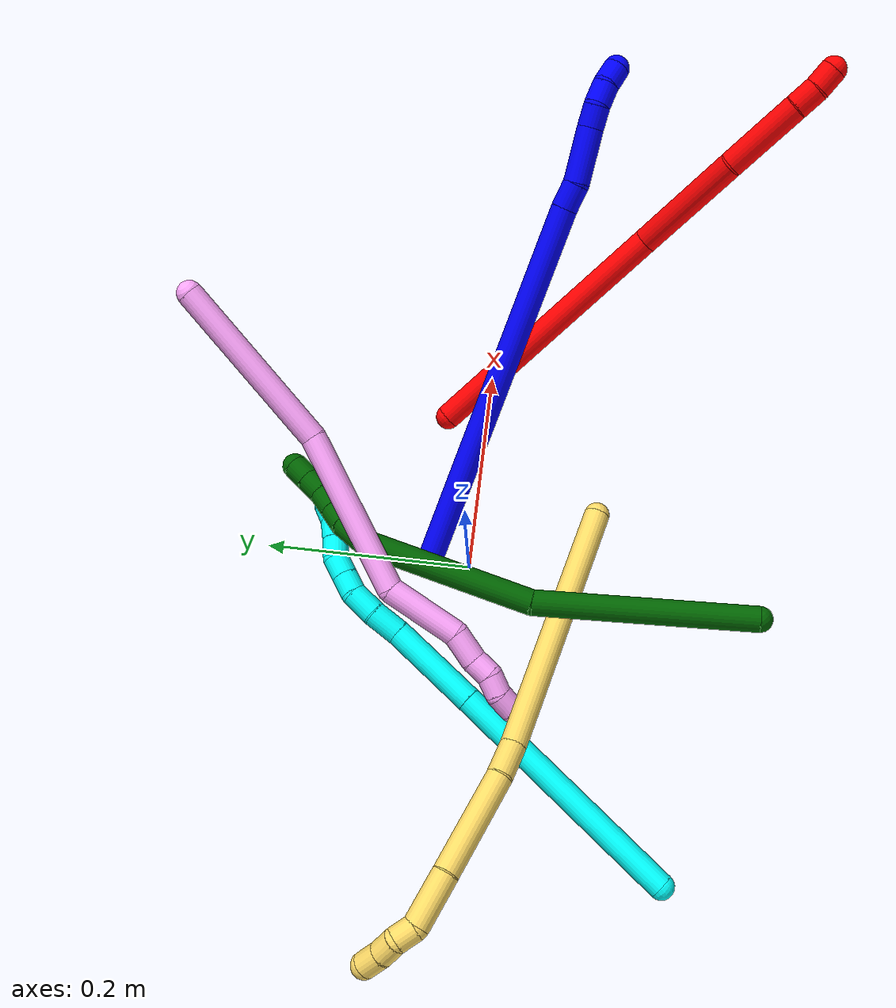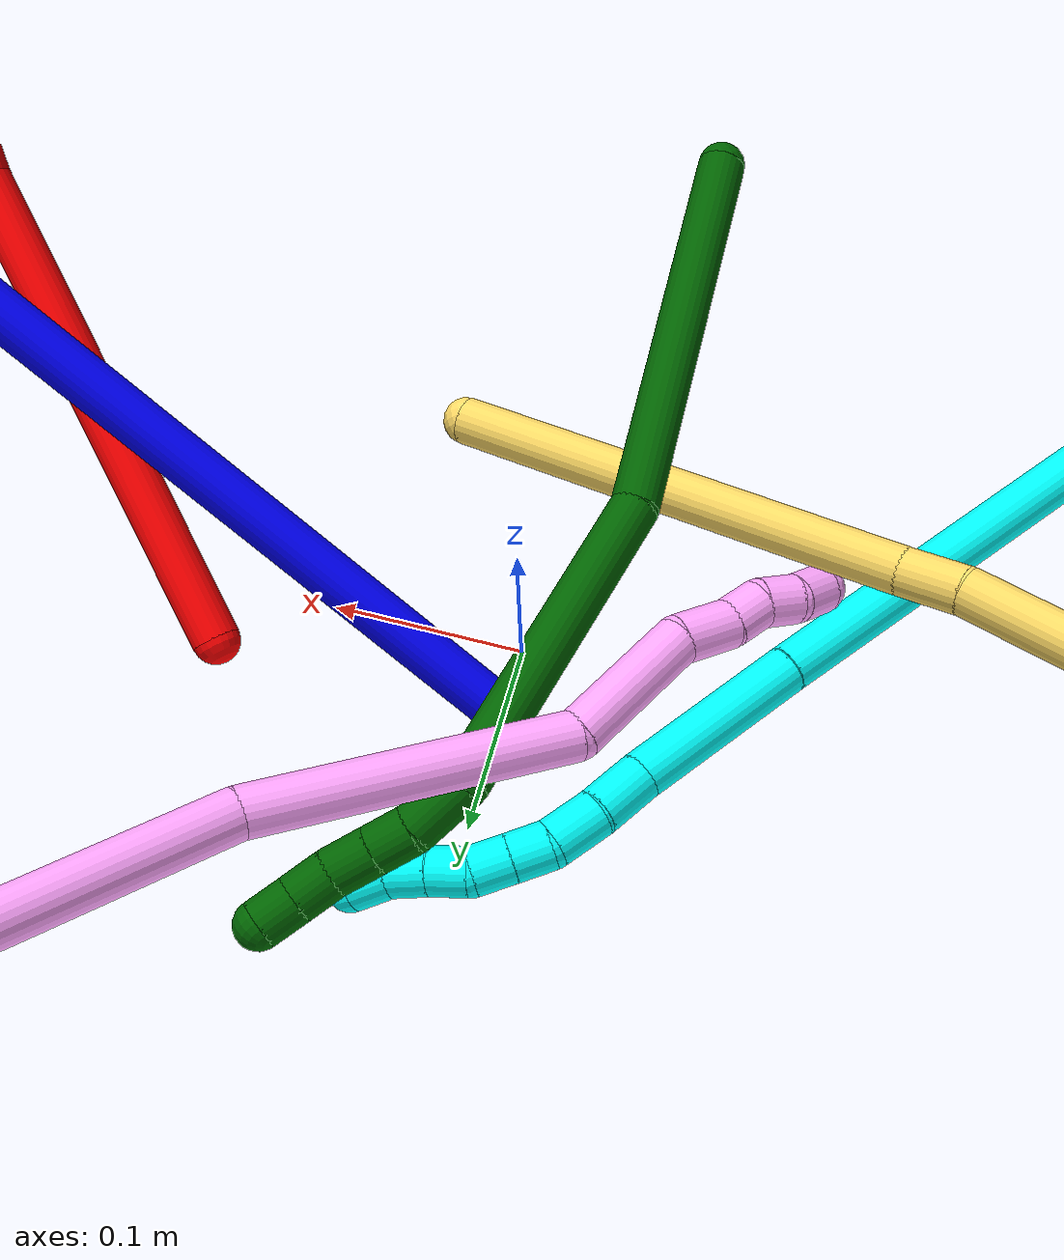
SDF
<sdf version="1.7">
 <world name="default">
  <plugin name="TubeGeneratorPlugin" filename="libtube_generator_plugin.so"/>
  <model name="photoneo_s_sensor">
   <static>1</static>
   <pose>0 0 2 1.57079 1.57079 3.14159</pose>
   <link name="link">
    <inertial><mass>0.1</mass></inertial>
    <sensor name="sensor" type="depth">
     <update_rate>30</update_rate>
     <camera>
      <horizontal_fov>1.22</horizontal_fov>
      <image><width>1920</width><height>1200</height><format>B8G8R8</format></image>
      <clip><near>0.1</near><far>4</far></clip>
      <depth_camera><output>points</output></depth_camera>
     </camera>
     <plugin name="camera_plugin" filename="libgazebo_ros_depth_camera.so">
      <baseline>0.2</baseline>
      <alwaysOn>1</alwaysOn>
      <updateRate>0.0</updateRate>
      <cameraName>camera_ir</cameraName>
      <imageTopicName>/camera/color/image_raw</imageTopicName>
      <cameraInfoTopicName>/camera/color/camera_info</cameraInfoTopicName>
      <depthImageTopicName>/camera/depth/image_raw</depthImageTopicName>
      <depthImageCameraInfoTopicName>/camera/depth/camera_info</depthImageCameraInfoTopicName>
      <pointCloudTopicName>/camera/depth/points</pointCloudTopicName>
      <frameName>fr_optical</frameName>
      <pointCloudCutoff>0.1</pointCloudCutoff>
      <pointCloudCutoffMax>2.0</pointCloudCutoffMax>
      <distortionK1>0</distortionK1>
      <distortionK2>0</distortionK2>
      <distortionK3>0</distortionK3>
      <distortionT1>0</distortionT1>
      <distortionT2>0</distortionT2>
      <CxPrime>0</CxPrime>
      <Cx>0</Cx>
      <Cy>0</Cy>
      <focalLength>0</focalLength>
      <hackBaseline>0</hackBaseline>
     </plugin>
    </sensor>
   </link>
  </model>
  <gravity>0 0 -9.8</gravity>
  <magnetic_field>6e-06 2.3e-05 -4.2e-05</magnetic_field>
  <atmosphere type="adiabatic"/>
  <physics name="default_physics" default="0" type="ode">
   <max_step_size>0.003</max_step_size>
   <real_time_factor>1</real_time_factor>
   <real_time_update_rate>1000</real_time_update_rate>
   <max_contacts>10000</max_contacts>
   <ode>
    <solver>
     <type>quick</type>
     <iters>100</iters>
     <sor>1.3</sor>
     <use_dynamic_moi_rescaling>0</use_dynamic_moi_rescaling>
    </solver>
    <constraints>
     <contact_max_correcting_vel>0</contact_max_correcting_vel>
     <contact_surface_layer>0.001</contact_surface_layer>
     <cfm>0</cfm>
     <erp>0.2</erp>
    </constraints>
   </ode>
  </physics>
  <scene><ambient>0.4 0.4 0.4 1</ambient><background>0.7 0.7 0.7 1</background><shadows>0</shadows></scene>
  <audio><device>default</device></audio>
  <spherical_coordinates>
   <surface_model>EARTH_WGS84</surface_model>
   <latitude_deg>0</latitude_deg>
   <longitude_deg>0</longitude_deg>
   <elevation>0</elevation>
   <heading_deg>0</heading_deg>
  </spherical_coordinates>
  <model name="bin">
   <static>1</static>
   <link name="bottom">
    <collision name="collision-bottom">
     <pose>0 0 -0.01 0 -0 0</pose>
     <geometry><box><size>0.8 0.6 0.02</size></box></geometry>
     <surface>
      <friction><ode><mu>100</mu><mu2>100</mu2></ode></friction>
      <contact><collide_bitmask>65535</collide_bitmask></contact>
     </surface>
    </collision>
   </link>
   <link name="west_wall">
    <collision name="collision-west_wall">
     <pose>-0.41 0 0.1 0 -0 0</pose>
     <geometry><box><size>0.02 0.6 0.2</size></box></geometry>
     <surface>
      <friction><ode><mu>100</mu><mu2>100</mu2></ode></friction>
      <contact><collide_bitmask>65535</collide_bitmask></contact>
     </surface>
    </collision>
   </link>
   <link name="east_wall">
    <collision name="collision-east_wall">
     <pose>0.41 0 0.1 0 -0 0</pose>
     <geometry><box><size>0.02 0.6 0.2</size></box></geometry>
     <surface>
      <friction><ode><mu>100</mu><mu2>100</mu2></ode></friction>
      <contact><collide_bitmask>65535</collide_bitmask></contact>
     </surface>
    </collision>
   </link>
   <link name="south_wall">
    <collision name="collision-south_wall">
     <pose>0 -0.31 0.1 0 -0 0</pose>
     <geometry><box><size>0.8 0.02 0.2</size></box></geometry>
     <surface>
      <friction><ode><mu>100</mu><mu2>100</mu2></ode></friction>
      <contact><collide_bitmask>65535</collide_bitmask></contact>
     </surface>
    </collision>
   </link>
   <link name="north_wall">
    <collision name="collision-north_wall">
     <pose>0 0.31 0.1 0 -0 0</pose>
     <geometry><box><size>0.8 0.02 0.2</size></box></geometry>
     <surface>
      <friction><ode><mu>100</mu><mu2>100</mu2></ode></friction>
      <contact><collide_bitmask>65535</collide_bitmask></contact>
     </surface>
    </collision>
   </link>
  </model>
  <model name="1">
   <static>0</static>
   <link name="1">
    <collision name="collision-cylinder-e_1_1_4">
     <pose>0.032209 -0.00201 0.176955 0.011359 0.180038 0.001025</pose>
     <geometry><cylinder><radius>0.0125</radius><length>0.359748</length></cylinder></geometry>
     <surface>
      <friction><ode><mu>1.16</mu><mu2>1.16</mu2><slip1>0</slip1><slip2>0</slip2></ode></friction>
      <contact><ode><kp>1e+06</kp><kd>1</kd><max_vel>0</max_vel><min_depth>0.001</min_depth></ode></contact>
     </surface>
    </collision>
    <visual name="visual-cylinder-e_1_1_4">
     <pose>0.032209 -0.00201 0.176955 0.011359 0.180038 0.001025</pose>
     <geometry><cylinder><radius>0.0125</radius><length>0.359748</length></cylinder></geometry>
     <material><ambient>0 0 1 1</ambient></material>
    </visual>
    <collision name="collision-cylinder-e_2_4_5">
     <pose>0.065605 -0.005033 0.366294 0.081606 0.095205 0.00389</pose>
     <geometry><cylinder><radius>0.0125</radius><length>0.024962</length></cylinder></geometry>
     <surface>
      <friction><ode><mu>1.16</mu><mu2>1.16</mu2><slip1>0</slip1><slip2>0</slip2></ode></friction>
      <contact><ode><kp>1e+06</kp><kd>1</kd><max_vel>0</max_vel><min_depth>0.001</min_depth></ode></contact>
     </surface>
    </collision>
    <visual name="visual-cylinder-e_2_4_5">
     <pose>0.065605 -0.005033 0.366294 0.081606 0.095205 0.00389</pose>
     <geometry><cylinder><radius>0.0125</radius><length>0.024962</length></cylinder></geometry>
     <material><ambient>0 0 1 1</ambient></material>
    </visual>
    <collision name="collision-cylinder-e_3_5_6">
     <pose>0.073636 -0.003648 0.403814 -0.095113 0.264665 -0.01267</pose>
     <geometry><cylinder><radius>0.0125</radius><length>0.052325</length></cylinder></geometry>
     <surface>
      <friction><ode><mu>1.16</mu><mu2>1.16</mu2><slip1>0</slip1><slip2>0</slip2></ode></friction>
      <contact><ode><kp>1e+06</kp><kd>1</kd><max_vel>0</max_vel><min_depth>0.001</min_depth></ode></contact>
     </surface>
    </collision>
    <visual name="visual-cylinder-e_3_5_6">
     <pose>0.073636 -0.003648 0.403814 -0.095113 0.264665 -0.01267</pose>
     <geometry><cylinder><radius>0.0125</radius><length>0.052325</length></cylinder></geometry>
     <material><ambient>0 0 1 1</ambient></material>
    </visual>
    <collision name="collision-cylinder-e_4_6_7">
     <pose>0.082301 -0.000454 0.43939 -0.076038 0.172275 -0.006569</pose>
     <geometry><cylinder><radius>0.0125</radius><length>0.021251</length></cylinder></geometry>
     <surface>
      <friction><ode><mu>1.16</mu><mu2>1.16</mu2><slip1>0</slip1><slip2>0</slip2></ode></friction>
      <contact><ode><kp>1e+06</kp><kd>1</kd><max_vel>0</max_vel><min_depth>0.001</min_depth></ode></contact>
     </surface>
    </collision>
    <visual name="visual-cylinder-e_4_6_7">
     <pose>0.082301 -0.000454 0.43939 -0.076038 0.172275 -0.006569</pose>
     <geometry><cylinder><radius>0.0125</radius><length>0.021251</length></cylinder></geometry>
     <material><ambient>0 0 1 1</ambient></material>
    </visual>
    <collision name="collision-cylinder-e_5_7_8">
     <pose>0.08855 -0.000685 0.459422 0.106512 0.4302 0.023292</pose>
     <geometry><cylinder><radius>0.0125</radius><length>0.021231</length></cylinder></geometry>
     <surface>
      <friction><ode><mu>1.16</mu><mu2>1.16</mu2><slip1>0</slip1><slip2>0</slip2></ode></friction>
      <contact><ode><kp>1e+06</kp><kd>1</kd><max_vel>0</max_vel><min_depth>0.001</min_depth></ode></contact>
     </surface>
    </collision>
    <visual name="visual-cylinder-e_5_7_8">
     <pose>0.08855 -0.000685 0.459422 0.106512 0.4302 0.023292</pose>
     <geometry><cylinder><radius>0.0125</radius><length>0.021231</length></cylinder></geometry>
     <material><ambient>0 0 1 1</ambient></material>
    </visual>
    <collision name="collision-cylinder-e_6_8_2">
     <pose>0.098593 -0.004645 0.477061 0.349736 0.580467 0.105435</pose>
     <geometry><cylinder><radius>0.0125</radius><length>0.020482</length></cylinder></geometry>
     <surface>
      <friction><ode><mu>1.16</mu><mu2>1.16</mu2><slip1>0</slip1><slip2>0</slip2></ode></friction>
      <contact><ode><kp>1e+06</kp><kd>1</kd><max_vel>0</max_vel><min_depth>0.001</min_depth></ode></contact>
     </surface>
    </collision>
    <visual name="visual-cylinder-e_6_8_2">
     <pose>0.098593 -0.004645 0.477061 0.349736 0.580467 0.105435</pose>
     <geometry><cylinder><radius>0.0125</radius><length>0.020482</length></cylinder></geometry>
     <material><ambient>0 0 1 1</ambient></material>
    </visual>
    <collision name="collision-sphere-2">
     <pose>0.10421 -0.007579 0.485106 0 -0 0</pose>
     <geometry><sphere><radius>0.0125</radius></sphere></geometry>
     <surface>
      <friction><ode><mu>1.16</mu><mu2>1.16</mu2><slip1>0</slip1><slip2>0</slip2></ode></friction>
      <contact><ode><kp>1e+06</kp><kd>1</kd><max_vel>0</max_vel><min_depth>0.001</min_depth></ode></contact>
     </surface>
    </collision>
    <visual name="visual-sphere-2">
     <pose>0.10421 -0.007579 0.485106 0 -0 0</pose>
     <geometry><sphere><radius>0.0125</radius></sphere></geometry>
     <material><ambient>0 0 1 1</ambient></material>
    </visual>
    <collision name="collision-sphere-4">
     <pose>0.064419 -0.00402 0.353911 0 -0 0</pose>
     <geometry><sphere><radius>0.0125</radius></sphere></geometry>
     <surface>
      <friction><ode><mu>1.16</mu><mu2>1.16</mu2><slip1>0</slip1><slip2>0</slip2></ode></friction>
      <contact><ode><kp>1e+06</kp><kd>1</kd><max_vel>0</max_vel><min_depth>0.001</min_depth></ode></contact>
     </surface>
    </collision>
    <visual name="visual-sphere-4">
     <pose>0.064419 -0.00402 0.353911 0 -0 0</pose>
     <geometry><sphere><radius>0.0125</radius></sphere></geometry>
     <material><ambient>0 0 1 1</ambient></material>
    </visual>
    <collision name="collision-sphere-1">
     <geometry><sphere><radius>0.0125</radius></sphere></geometry>
     <surface>
      <friction><ode><mu>1.16</mu><mu2>1.16</mu2><slip1>0</slip1><slip2>0</slip2></ode></friction>
      <contact><ode><kp>1e+06</kp><kd>1</kd><max_vel>0</max_vel><min_depth>0.001</min_depth></ode></contact>
     </surface>
    </collision>
    <visual name="visual-sphere-1">
     <geometry><sphere><radius>0.0125</radius></sphere></geometry>
     <material><ambient>0 0 1 1</ambient></material>
    </visual>
    <collision name="collision-sphere-8">
     <pose>0.092977 -0.00171 0.469015 0 -0 0</pose>
     <geometry><sphere><radius>0.0125</radius></sphere></geometry>
     <surface>
      <friction><ode><mu>1.16</mu><mu2>1.16</mu2><slip1>0</slip1><slip2>0</slip2></ode></friction>
      <contact><ode><kp>1e+06</kp><kd>1</kd><max_vel>0</max_vel><min_depth>0.001</min_depth></ode></contact>
     </surface>
    </collision>
    <visual name="visual-sphere-8">
     <pose>0.092977 -0.00171 0.469015 0 -0 0</pose>
     <geometry><sphere><radius>0.0125</radius></sphere></geometry>
     <material><ambient>0 0 1 1</ambient></material>
    </visual>
    <collision name="collision-sphere-5">
     <pose>0.066792 -0.006046 0.378677 0 -0 0</pose>
     <geometry><sphere><radius>0.0125</radius></sphere></geometry>
     <surface>
      <friction><ode><mu>1.16</mu><mu2>1.16</mu2><slip1>0</slip1><slip2>0</slip2></ode></friction>
      <contact><ode><kp>1e+06</kp><kd>1</kd><max_vel>0</max_vel><min_depth>0.001</min_depth></ode></contact>
     </surface>
    </collision>
    <visual name="visual-sphere-5">
     <pose>0.066792 -0.006046 0.378677 0 -0 0</pose>
     <geometry><sphere><radius>0.0125</radius></sphere></geometry>
     <material><ambient>0 0 1 1</ambient></material>
    </visual>
    <collision name="collision-sphere-6">
     <pose>0.080479 -0.00125 0.428952 0 -0 0</pose>
     <geometry><sphere><radius>0.0125</radius></sphere></geometry>
     <surface>
      <friction><ode><mu>1.16</mu><mu2>1.16</mu2><slip1>0</slip1><slip2>0</slip2></ode></friction>
      <contact><ode><kp>1e+06</kp><kd>1</kd><max_vel>0</max_vel><min_depth>0.001</min_depth></ode></contact>
     </surface>
    </collision>
    <visual name="visual-sphere-6">
     <pose>0.080479 -0.00125 0.428952 0 -0 0</pose>
     <geometry><sphere><radius>0.0125</radius></sphere></geometry>
     <material><ambient>0 0 1 1</ambient></material>
    </visual>
    <collision name="collision-sphere-7">
     <pose>0.084122 0.000341 0.449828 0 -0 0</pose>
     <geometry><sphere><radius>0.0125</radius></sphere></geometry>
     <surface>
      <friction><ode><mu>1.16</mu><mu2>1.16</mu2><slip1>0</slip1><slip2>0</slip2></ode></friction>
      <contact><ode><kp>1e+06</kp><kd>1</kd><max_vel>0</max_vel><min_depth>0.001</min_depth></ode></contact>
     </surface>
    </collision>
    <visual name="visual-sphere-7">
     <pose>0.084122 0.000341 0.449828 0 -0 0</pose>
     <geometry><sphere><radius>0.0125</radius></sphere></geometry>
     <material><ambient>0 0 1 1</ambient></material>
    </visual>
    <inertial>
     <pose>0.045453 -0.002318 0.245591 0 -0 0</pose>
     <mass>0.5</mass>
     <inertia>
      <ixx>0.003863</ixx>
      <ixy>0</ixy>
      <ixz>0</ixz>
      <iyy>0.003918</iyy>
      <iyz>0</iyz>
      <izz>-0.000622</izz>
     </inertia>
    </inertial>
   </link>
   <pose>0.002924 0.03829 0.012201 0.490272 0.84455 0.257137</pose>
  </model>
  <model name="2">
   <static>0</static>
   <link name="2">
    <collision name="collision-cylinder-e_1_1_4">
     <pose>0.001031 -0.00292 0.130881 0.022304 0.007878 8.8e-05</pose>
     <geometry><cylinder><radius>0.0125</radius><length>0.261836</length></cylinder></geometry>
     <surface>
      <friction><ode><mu>1.16</mu><mu2>1.16</mu2><slip1>0</slip1><slip2>0</slip2></ode></friction>
      <contact><ode><kp>1e+06</kp><kd>1</kd><max_vel>0</max_vel><min_depth>0.001</min_depth></ode></contact>
     </surface>
    </collision>
    <visual name="visual-cylinder-e_1_1_4">
     <pose>0.001031 -0.00292 0.130881 0.022304 0.007878 8.8e-05</pose>
     <geometry><cylinder><radius>0.0125</radius><length>0.261836</length></cylinder></geometry>
     <material><ambient>1 0 0 1</ambient></material>
    </visual>
    <collision name="collision-cylinder-e_2_4_5">
     <pose>0.017242 -0.021675 0.314405 0.292199 0.269409 0.039879</pose>
     <geometry><cylinder><radius>0.0125</radius><length>0.114059</length></cylinder></geometry>
     <surface>
      <friction><ode><mu>1.16</mu><mu2>1.16</mu2><slip1>0</slip1><slip2>0</slip2></ode></friction>
      <contact><ode><kp>1e+06</kp><kd>1</kd><max_vel>0</max_vel><min_depth>0.001</min_depth></ode></contact>
     </surface>
    </collision>
    <visual name="visual-cylinder-e_2_4_5">
     <pose>0.017242 -0.021675 0.314405 0.292199 0.269409 0.039879</pose>
     <geometry><cylinder><radius>0.0125</radius><length>0.114059</length></cylinder></geometry>
     <material><ambient>1 0 0 1</ambient></material>
    </visual>
    <collision name="collision-cylinder-e_3_5_6">
     <pose>0.037585 -0.042995 0.405016 0.143471 0.133797 0.009629</pose>
     <geometry><cylinder><radius>0.0125</radius><length>0.077419</length></cylinder></geometry>
     <surface>
      <friction><ode><mu>1.16</mu><mu2>1.16</mu2><slip1>0</slip1><slip2>0</slip2></ode></friction>
      <contact><ode><kp>1e+06</kp><kd>1</kd><max_vel>0</max_vel><min_depth>0.001</min_depth></ode></contact>
     </surface>
    </collision>
    <visual name="visual-cylinder-e_3_5_6">
     <pose>0.037585 -0.042995 0.405016 0.143471 0.133797 0.009629</pose>
     <geometry><cylinder><radius>0.0125</radius><length>0.077419</length></cylinder></geometry>
     <material><ambient>1 0 0 1</ambient></material>
    </visual>
    <collision name="collision-cylinder-e_4_6_7">
     <pose>0.043498 -0.049268 0.455108 0.064909 0.061589 0.002</pose>
     <geometry><cylinder><radius>0.0125</radius><length>0.024342</length></cylinder></geometry>
     <surface>
      <friction><ode><mu>1.16</mu><mu2>1.16</mu2><slip1>0</slip1><slip2>0</slip2></ode></friction>
      <contact><ode><kp>1e+06</kp><kd>1</kd><max_vel>0</max_vel><min_depth>0.001</min_depth></ode></contact>
     </surface>
    </collision>
    <visual name="visual-cylinder-e_4_6_7">
     <pose>0.043498 -0.049268 0.455108 0.064909 0.061589 0.002</pose>
     <geometry><cylinder><radius>0.0125</radius><length>0.024342</length></cylinder></geometry>
     <material><ambient>1 0 0 1</ambient></material>
    </visual>
    <collision name="collision-cylinder-e_5_7_2">
     <pose>0.042804 -0.050937 0.478274 0.079582 -0.129528 -0.005164</pose>
     <geometry><cylinder><radius>0.0125</radius><length>0.022344</length></cylinder></geometry>
     <surface>
      <friction><ode><mu>1.16</mu><mu2>1.16</mu2><slip1>0</slip1><slip2>0</slip2></ode></friction>
      <contact><ode><kp>1e+06</kp><kd>1</kd><max_vel>0</max_vel><min_depth>0.001</min_depth></ode></contact>
     </surface>
    </collision>
    <visual name="visual-cylinder-e_5_7_2">
     <pose>0.042804 -0.050937 0.478274 0.079582 -0.129528 -0.005164</pose>
     <geometry><cylinder><radius>0.0125</radius><length>0.022344</length></cylinder></geometry>
     <material><ambient>1 0 0 1</ambient></material>
    </visual>
    <collision name="collision-sphere-2">
     <pose>0.041361 -0.051818 0.489317 0 -0 0</pose>
     <geometry><sphere><radius>0.0125</radius></sphere></geometry>
     <surface>
      <friction><ode><mu>1.16</mu><mu2>1.16</mu2><slip1>0</slip1><slip2>0</slip2></ode></friction>
      <contact><ode><kp>1e+06</kp><kd>1</kd><max_vel>0</max_vel><min_depth>0.001</min_depth></ode></contact>
     </surface>
    </collision>
    <visual name="visual-sphere-2">
     <pose>0.041361 -0.051818 0.489317 0 -0 0</pose>
     <geometry><sphere><radius>0.0125</radius></sphere></geometry>
     <material><ambient>1 0 0 1</ambient></material>
    </visual>
    <collision name="collision-sphere-7">
     <pose>0.044247 -0.050056 0.467231 0 -0 0</pose>
     <geometry><sphere><radius>0.0125</radius></sphere></geometry>
     <surface>
      <friction><ode><mu>1.16</mu><mu2>1.16</mu2><slip1>0</slip1><slip2>0</slip2></ode></friction>
      <contact><ode><kp>1e+06</kp><kd>1</kd><max_vel>0</max_vel><min_depth>0.001</min_depth></ode></contact>
     </surface>
    </collision>
    <visual name="visual-sphere-7">
     <pose>0.044247 -0.050056 0.467231 0 -0 0</pose>
     <geometry><sphere><radius>0.0125</radius></sphere></geometry>
     <material><ambient>1 0 0 1</ambient></material>
    </visual>
    <collision name="collision-sphere-6">
     <pose>0.042749 -0.04848 0.442986 0 -0 0</pose>
     <geometry><sphere><radius>0.0125</radius></sphere></geometry>
     <surface>
      <friction><ode><mu>1.16</mu><mu2>1.16</mu2><slip1>0</slip1><slip2>0</slip2></ode></friction>
      <contact><ode><kp>1e+06</kp><kd>1</kd><max_vel>0</max_vel><min_depth>0.001</min_depth></ode></contact>
     </surface>
    </collision>
    <visual name="visual-sphere-6">
     <pose>0.042749 -0.04848 0.442986 0 -0 0</pose>
     <geometry><sphere><radius>0.0125</radius></sphere></geometry>
     <material><ambient>1 0 0 1</ambient></material>
    </visual>
    <collision name="collision-sphere-5">
     <pose>0.032421 -0.03751 0.367047 0 -0 0</pose>
     <geometry><sphere><radius>0.0125</radius></sphere></geometry>
     <surface>
      <friction><ode><mu>1.16</mu><mu2>1.16</mu2><slip1>0</slip1><slip2>0</slip2></ode></friction>
      <contact><ode><kp>1e+06</kp><kd>1</kd><max_vel>0</max_vel><min_depth>0.001</min_depth></ode></contact>
     </surface>
    </collision>
    <visual name="visual-sphere-5">
     <pose>0.032421 -0.03751 0.367047 0 -0 0</pose>
     <geometry><sphere><radius>0.0125</radius></sphere></geometry>
     <material><ambient>1 0 0 1</ambient></material>
    </visual>
    <collision name="collision-sphere-1">
     <geometry><sphere><radius>0.0125</radius></sphere></geometry>
     <surface>
      <friction><ode><mu>1.16</mu><mu2>1.16</mu2><slip1>0</slip1><slip2>0</slip2></ode></friction>
      <contact><ode><kp>1e+06</kp><kd>1</kd><max_vel>0</max_vel><min_depth>0.001</min_depth></ode></contact>
     </surface>
    </collision>
    <visual name="visual-sphere-1">
     <geometry><sphere><radius>0.0125</radius></sphere></geometry>
     <material><ambient>1 0 0 1</ambient></material>
    </visual>
    <collision name="collision-sphere-4">
     <pose>0.002063 -0.005839 0.261762 0 -0 0</pose>
     <geometry><sphere><radius>0.0125</radius></sphere></geometry>
     <surface>
      <friction><ode><mu>1.16</mu><mu2>1.16</mu2><slip1>0</slip1><slip2>0</slip2></ode></friction>
      <contact><ode><kp>1e+06</kp><kd>1</kd><max_vel>0</max_vel><min_depth>0.001</min_depth></ode></contact>
     </surface>
    </collision>
    <visual name="visual-sphere-4">
     <pose>0.002063 -0.005839 0.261762 0 -0 0</pose>
     <geometry><sphere><radius>0.0125</radius></sphere></geometry>
     <material><ambient>1 0 0 1</ambient></material>
    </visual>
    <inertial>
     <pose>0.014323 -0.017805 0.246502 0 -0 0</pose>
     <mass>0.5</mass>
     <inertia>
      <ixx>0.001683</ixx>
      <ixy>0</ixy>
      <ixz>0</ixz>
      <iyy>0.001675</iyy>
      <iyz>0</iyz>
      <izz>6.2e-05</izz>
     </inertia>
    </inertial>
   </link>
   <pose>0.150536 0.038804 0.011521 -1.17351 -0.453041 -2.5678</pose>
  </model>
  <model name="3">
   <static>0</static>
   <link name="3">
    <collision name="collision-cylinder-e_1_1_4">
     <pose>0.078538 0.093618 -0.020229 -1.78361 0.686818 -0.834195</pose>
     <geometry><cylinder><radius>0.0125</radius><length>0.247724</length></cylinder></geometry>
     <surface>
      <friction><ode><mu>1.16</mu><mu2>1.16</mu2><slip1>0</slip1><slip2>0</slip2></ode></friction>
      <contact><ode><kp>1e+06</kp><kd>1</kd><max_vel>0</max_vel><min_depth>0.001</min_depth></ode></contact>
     </surface>
    </collision>
    <visual name="visual-cylinder-e_1_1_4">
     <pose>0.078538 0.093618 -0.020229 -1.78361 0.686818 -0.834195</pose>
     <geometry><cylinder><radius>0.0125</radius><length>0.247724</length></cylinder></geometry>
     <material><ambient>0.003922 1 0.996078 1</ambient></material>
    </visual>
    <collision name="collision-cylinder-e_2_4_5">
     <pose>0.187927 0.221482 -0.049372 -1.82544 0.717 -0.902674</pose>
     <geometry><cylinder><radius>0.0125</radius><length>0.093894</length></cylinder></geometry>
     <surface>
      <friction><ode><mu>1.16</mu><mu2>1.16</mu2><slip1>0</slip1><slip2>0</slip2></ode></friction>
      <contact><ode><kp>1e+06</kp><kd>1</kd><max_vel>0</max_vel><min_depth>0.001</min_depth></ode></contact>
     </surface>
    </collision>
    <visual name="visual-cylinder-e_2_4_5">
     <pose>0.187927 0.221482 -0.049372 -1.82544 0.717 -0.902674</pose>
     <geometry><cylinder><radius>0.0125</radius><length>0.093894</length></cylinder></geometry>
     <material><ambient>0.003922 1 0.996078 1</ambient></material>
    </visual>
    <collision name="collision-cylinder-e_3_5_6">
     <pose>0.226467 0.268558 -0.061314 -1.80255 0.528135 -0.658378</pose>
     <geometry><cylinder><radius>0.0125</radius><length>0.030521</length></cylinder></geometry>
     <surface>
      <friction><ode><mu>1.16</mu><mu2>1.16</mu2><slip1>0</slip1><slip2>0</slip2></ode></friction>
      <contact><ode><kp>1e+06</kp><kd>1</kd><max_vel>0</max_vel><min_depth>0.001</min_depth></ode></contact>
     </surface>
    </collision>
    <visual name="visual-cylinder-e_3_5_6">
     <pose>0.226467 0.268558 -0.061314 -1.80255 0.528135 -0.658378</pose>
     <geometry><cylinder><radius>0.0125</radius><length>0.030521</length></cylinder></geometry>
     <material><ambient>0.003922 1 0.996078 1</ambient></material>
    </visual>
    <collision name="collision-cylinder-e_4_6_7">
     <pose>0.242831 0.291801 -0.066439 -1.76957 0.684677 -0.821147</pose>
     <geometry><cylinder><radius>0.0125</radius><length>0.02743</length></cylinder></geometry>
     <surface>
      <friction><ode><mu>1.16</mu><mu2>1.16</mu2><slip1>0</slip1><slip2>0</slip2></ode></friction>
      <contact><ode><kp>1e+06</kp><kd>1</kd><max_vel>0</max_vel><min_depth>0.001</min_depth></ode></contact>
     </surface>
    </collision>
    <visual name="visual-cylinder-e_4_6_7">
     <pose>0.242831 0.291801 -0.066439 -1.76957 0.684677 -0.821147</pose>
     <geometry><cylinder><radius>0.0125</radius><length>0.02743</length></cylinder></geometry>
     <material><ambient>0.003922 1 0.996078 1</ambient></material>
    </visual>
    <collision name="collision-cylinder-e_5_7_8">
     <pose>0.259669 0.308036 -0.067935 -1.46769 0.948958 -0.867569</pose>
     <geometry><cylinder><radius>0.0125</radius><length>0.02009</length></cylinder></geometry>
     <surface>
      <friction><ode><mu>1.16</mu><mu2>1.16</mu2><slip1>0</slip1><slip2>0</slip2></ode></friction>
      <contact><ode><kp>1e+06</kp><kd>1</kd><max_vel>0</max_vel><min_depth>0.001</min_depth></ode></contact>
     </surface>
    </collision>
    <visual name="visual-cylinder-e_5_7_8">
     <pose>0.259669 0.308036 -0.067935 -1.46769 0.948958 -0.867569</pose>
     <geometry><cylinder><radius>0.0125</radius><length>0.02009</length></cylinder></geometry>
     <material><ambient>0.003922 1 0.996078 1</ambient></material>
    </visual>
    <collision name="collision-cylinder-e_6_8_9">
     <pose>0.276044 0.319681 -0.066633 -1.45121 0.950455 -0.856383</pose>
     <geometry><cylinder><radius>0.0125</radius><length>0.020182</length></cylinder></geometry>
     <surface>
      <friction><ode><mu>1.16</mu><mu2>1.16</mu2><slip1>0</slip1><slip2>0</slip2></ode></friction>
      <contact><ode><kp>1e+06</kp><kd>1</kd><max_vel>0</max_vel><min_depth>0.001</min_depth></ode></contact>
     </surface>
    </collision>
    <visual name="visual-cylinder-e_6_8_9">
     <pose>0.276044 0.319681 -0.066633 -1.45121 0.950455 -0.856383</pose>
     <geometry><cylinder><radius>0.0125</radius><length>0.020182</length></cylinder></geometry>
     <material><ambient>0.003922 1 0.996078 1</ambient></material>
    </visual>
    <collision name="collision-cylinder-e_7_9_10">
     <pose>0.293091 0.328651 -0.062309 -0.714928 1.07319 -0.437232</pose>
     <geometry><cylinder><radius>0.0125</radius><length>0.020111</length></cylinder></geometry>
     <surface>
      <friction><ode><mu>1.16</mu><mu2>1.16</mu2><slip1>0</slip1><slip2>0</slip2></ode></friction>
      <contact><ode><kp>1e+06</kp><kd>1</kd><max_vel>0</max_vel><min_depth>0.001</min_depth></ode></contact>
     </surface>
    </collision>
    <visual name="visual-cylinder-e_7_9_10">
     <pose>0.293091 0.328651 -0.062309 -0.714928 1.07319 -0.437232</pose>
     <geometry><cylinder><radius>0.0125</radius><length>0.020111</length></cylinder></geometry>
     <material><ambient>0.003922 1 0.996078 1</ambient></material>
    </visual>
    <collision name="collision-cylinder-e_8_10_11">
     <pose>0.310982 0.334972 -0.055856 -0.84295 1.13186 -0.554918</pose>
     <geometry><cylinder><radius>0.0125</radius><length>0.020007</length></cylinder></geometry>
     <surface>
      <friction><ode><mu>1.16</mu><mu2>1.16</mu2><slip1>0</slip1><slip2>0</slip2></ode></friction>
      <contact><ode><kp>1e+06</kp><kd>1</kd><max_vel>0</max_vel><min_depth>0.001</min_depth></ode></contact>
     </surface>
    </collision>
    <visual name="visual-cylinder-e_8_10_11">
     <pose>0.310982 0.334972 -0.055856 -0.84295 1.13186 -0.554918</pose>
     <geometry><cylinder><radius>0.0125</radius><length>0.020007</length></cylinder></geometry>
     <material><ambient>0.003922 1 0.996078 1</ambient></material>
    </visual>
    <collision name="collision-cylinder-e_9_11_2">
     <pose>0.329396 0.341729 -0.05307 -1.58267 1.20512 -1.21624</pose>
     <geometry><cylinder><radius>0.0125</radius><length>0.020042</length></cylinder></geometry>
     <surface>
      <friction><ode><mu>1.16</mu><mu2>1.16</mu2><slip1>0</slip1><slip2>0</slip2></ode></friction>
      <contact><ode><kp>1e+06</kp><kd>1</kd><max_vel>0</max_vel><min_depth>0.001</min_depth></ode></contact>
     </surface>
    </collision>
    <visual name="visual-cylinder-e_9_11_2">
     <pose>0.329396 0.341729 -0.05307 -1.58267 1.20512 -1.21624</pose>
     <geometry><cylinder><radius>0.0125</radius><length>0.020042</length></cylinder></geometry>
     <material><ambient>0.003922 1 0.996078 1</ambient></material>
    </visual>
    <collision name="collision-sphere-2">
     <pose>0.338754 0.345312 -0.053113 0 -0 0</pose>
     <geometry><sphere><radius>0.0125</radius></sphere></geometry>
     <surface>
      <friction><ode><mu>1.16</mu><mu2>1.16</mu2><slip1>0</slip1><slip2>0</slip2></ode></friction>
      <contact><ode><kp>1e+06</kp><kd>1</kd><max_vel>0</max_vel><min_depth>0.001</min_depth></ode></contact>
     </surface>
    </collision>
    <visual name="visual-sphere-2">
     <pose>0.338754 0.345312 -0.053113 0 -0 0</pose>
     <geometry><sphere><radius>0.0125</radius></sphere></geometry>
     <material><ambient>0.003922 1 0.996078 1</ambient></material>
    </visual>
    <collision name="collision-sphere-11">
     <pose>0.320038 0.338146 -0.053028 0 -0 0</pose>
     <geometry><sphere><radius>0.0125</radius></sphere></geometry>
     <surface>
      <friction><ode><mu>1.16</mu><mu2>1.16</mu2><slip1>0</slip1><slip2>0</slip2></ode></friction>
      <contact><ode><kp>1e+06</kp><kd>1</kd><max_vel>0</max_vel><min_depth>0.001</min_depth></ode></contact>
     </surface>
    </collision>
    <visual name="visual-sphere-11">
     <pose>0.320038 0.338146 -0.053028 0 -0 0</pose>
     <geometry><sphere><radius>0.0125</radius></sphere></geometry>
     <material><ambient>0.003922 1 0.996078 1</ambient></material>
    </visual>
    <collision name="collision-sphere-10">
     <pose>0.301927 0.331798 -0.058684 0 -0 0</pose>
     <geometry><sphere><radius>0.0125</radius></sphere></geometry>
     <surface>
      <friction><ode><mu>1.16</mu><mu2>1.16</mu2><slip1>0</slip1><slip2>0</slip2></ode></friction>
      <contact><ode><kp>1e+06</kp><kd>1</kd><max_vel>0</max_vel><min_depth>0.001</min_depth></ode></contact>
     </surface>
    </collision>
    <visual name="visual-sphere-10">
     <pose>0.301927 0.331798 -0.058684 0 -0 0</pose>
     <geometry><sphere><radius>0.0125</radius></sphere></geometry>
     <material><ambient>0.003922 1 0.996078 1</ambient></material>
    </visual>
    <collision name="collision-sphere-9">
     <pose>0.284255 0.325505 -0.065933 0 -0 0</pose>
     <geometry><sphere><radius>0.0125</radius></sphere></geometry>
     <surface>
      <friction><ode><mu>1.16</mu><mu2>1.16</mu2><slip1>0</slip1><slip2>0</slip2></ode></friction>
      <contact><ode><kp>1e+06</kp><kd>1</kd><max_vel>0</max_vel><min_depth>0.001</min_depth></ode></contact>
     </surface>
    </collision>
    <visual name="visual-sphere-9">
     <pose>0.284255 0.325505 -0.065933 0 -0 0</pose>
     <geometry><sphere><radius>0.0125</radius></sphere></geometry>
     <material><ambient>0.003922 1 0.996078 1</ambient></material>
    </visual>
    <collision name="collision-sphere-4">
     <pose>0.157077 0.187236 -0.040458 0 -0 0</pose>
     <geometry><sphere><radius>0.0125</radius></sphere></geometry>
     <surface>
      <friction><ode><mu>1.16</mu><mu2>1.16</mu2><slip1>0</slip1><slip2>0</slip2></ode></friction>
      <contact><ode><kp>1e+06</kp><kd>1</kd><max_vel>0</max_vel><min_depth>0.001</min_depth></ode></contact>
     </surface>
    </collision>
    <visual name="visual-sphere-4">
     <pose>0.157077 0.187236 -0.040458 0 -0 0</pose>
     <geometry><sphere><radius>0.0125</radius></sphere></geometry>
     <material><ambient>0.003922 1 0.996078 1</ambient></material>
    </visual>
    <collision name="collision-sphere-1">
     <geometry><sphere><radius>0.0125</radius></sphere></geometry>
     <surface>
      <friction><ode><mu>1.16</mu><mu2>1.16</mu2><slip1>0</slip1><slip2>0</slip2></ode></friction>
      <contact><ode><kp>1e+06</kp><kd>1</kd><max_vel>0</max_vel><min_depth>0.001</min_depth></ode></contact>
     </surface>
    </collision>
    <visual name="visual-sphere-1">
     <geometry><sphere><radius>0.0125</radius></sphere></geometry>
     <material><ambient>0.003922 1 0.996078 1</ambient></material>
    </visual>
    <collision name="collision-sphere-8">
     <pose>0.267834 0.313857 -0.067333 0 -0 0</pose>
     <geometry><sphere><radius>0.0125</radius></sphere></geometry>
     <surface>
      <friction><ode><mu>1.16</mu><mu2>1.16</mu2><slip1>0</slip1><slip2>0</slip2></ode></friction>
      <contact><ode><kp>1e+06</kp><kd>1</kd><max_vel>0</max_vel><min_depth>0.001</min_depth></ode></contact>
     </surface>
    </collision>
    <visual name="visual-sphere-8">
     <pose>0.267834 0.313857 -0.067333 0 -0 0</pose>
     <geometry><sphere><radius>0.0125</radius></sphere></geometry>
     <material><ambient>0.003922 1 0.996078 1</ambient></material>
    </visual>
    <collision name="collision-sphere-5">
     <pose>0.218777 0.255729 -0.058286 0 -0 0</pose>
     <geometry><sphere><radius>0.0125</radius></sphere></geometry>
     <surface>
      <friction><ode><mu>1.16</mu><mu2>1.16</mu2><slip1>0</slip1><slip2>0</slip2></ode></friction>
      <contact><ode><kp>1e+06</kp><kd>1</kd><max_vel>0</max_vel><min_depth>0.001</min_depth></ode></contact>
     </surface>
    </collision>
    <visual name="visual-sphere-5">
     <pose>0.218777 0.255729 -0.058286 0 -0 0</pose>
     <geometry><sphere><radius>0.0125</radius></sphere></geometry>
     <material><ambient>0.003922 1 0.996078 1</ambient></material>
    </visual>
    <collision name="collision-sphere-6">
     <pose>0.234157 0.281387 -0.064342 0 -0 0</pose>
     <geometry><sphere><radius>0.0125</radius></sphere></geometry>
     <surface>
      <friction><ode><mu>1.16</mu><mu2>1.16</mu2><slip1>0</slip1><slip2>0</slip2></ode></friction>
      <contact><ode><kp>1e+06</kp><kd>1</kd><max_vel>0</max_vel><min_depth>0.001</min_depth></ode></contact>
     </surface>
    </collision>
    <visual name="visual-sphere-6">
     <pose>0.234157 0.281387 -0.064342 0 -0 0</pose>
     <geometry><sphere><radius>0.0125</radius></sphere></geometry>
     <material><ambient>0.003922 1 0.996078 1</ambient></material>
    </visual>
    <collision name="collision-sphere-7">
     <pose>0.251505 0.302216 -0.068537 0 -0 0</pose>
     <geometry><sphere><radius>0.0125</radius></sphere></geometry>
     <surface>
      <friction><ode><mu>1.16</mu><mu2>1.16</mu2><slip1>0</slip1><slip2>0</slip2></ode></friction>
      <contact><ode><kp>1e+06</kp><kd>1</kd><max_vel>0</max_vel><min_depth>0.001</min_depth></ode></contact>
     </surface>
    </collision>
    <visual name="visual-sphere-7">
     <pose>0.251505 0.302216 -0.068537 0 -0 0</pose>
     <geometry><sphere><radius>0.0125</radius></sphere></geometry>
     <material><ambient>0.003922 1 0.996078 1</ambient></material>
    </visual>
    <inertial>
     <pose>0.160359 0.185976 -0.038969 0 -0 0</pose>
     <mass>0.5</mass>
     <inertia>
      <ixx>-5e-05</ixx>
      <ixy>0</ixy>
      <ixz>0</ixz>
      <iyy>-0.000316</iyy>
      <iyz>0</iyz>
      <izz>-0.001897</izz>
     </inertia>
    </inertial>
   </link>
   <pose>-0.284411 -0.211915 0.01149 0.905758 0.614323 0.278047</pose>
  </model>
  <model name="4">
   <static>0</static>
   <link name="4">
    <collision name="collision-cylinder-e_1_1_4">
     <pose>-0.032705 -0.030009 -0.075829 2.76476 -0.381403 -1.58314</pose>
     <geometry><cylinder><radius>0.0125</radius><length>0.17573</length></cylinder></geometry>
     <surface>
      <friction><ode><mu>1.16</mu><mu2>1.16</mu2><slip1>0</slip1><slip2>0</slip2></ode></friction>
      <contact><ode><kp>1e+06</kp><kd>1</kd><max_vel>0</max_vel><min_depth>0.001</min_depth></ode></contact>
     </surface>
    </collision>
    <visual name="visual-cylinder-e_1_1_4">
     <pose>-0.032705 -0.030009 -0.075829 2.76476 -0.381403 -1.58314</pose>
     <geometry><cylinder><radius>0.0125</radius><length>0.17573</length></cylinder></geometry>
     <material><ambient>1 0.65098 0.996078 1</ambient></material>
    </visual>
    <collision name="collision-cylinder-e_2_4_5">
     <pose>-0.112379 -0.076091 -0.21438 2.89073 -0.627573 -2.40038</pose>
     <geometry><cylinder><radius>0.0125</radius><length>0.15998</length></cylinder></geometry>
     <surface>
      <friction><ode><mu>1.16</mu><mu2>1.16</mu2><slip1>0</slip1><slip2>0</slip2></ode></friction>
      <contact><ode><kp>1e+06</kp><kd>1</kd><max_vel>0</max_vel><min_depth>0.001</min_depth></ode></contact>
     </surface>
    </collision>
    <visual name="visual-cylinder-e_2_4_5">
     <pose>-0.112379 -0.076091 -0.21438 2.89073 -0.627573 -2.40038</pose>
     <geometry><cylinder><radius>0.0125</radius><length>0.15998</length></cylinder></geometry>
     <material><ambient>1 0.65098 0.996078 1</ambient></material>
    </visual>
    <collision name="collision-cylinder-e_3_5_6">
     <pose>-0.169584 -0.114076 -0.304979 2.47543 -0.281026 -0.776193</pose>
     <geometry><cylinder><radius>0.0125</radius><length>0.073811</length></cylinder></geometry>
     <surface>
      <friction><ode><mu>1.16</mu><mu2>1.16</mu2><slip1>0</slip1><slip2>0</slip2></ode></friction>
      <contact><ode><kp>1e+06</kp><kd>1</kd><max_vel>0</max_vel><min_depth>0.001</min_depth></ode></contact>
     </surface>
    </collision>
    <visual name="visual-cylinder-e_3_5_6">
     <pose>-0.169584 -0.114076 -0.304979 2.47543 -0.281026 -0.776193</pose>
     <geometry><cylinder><radius>0.0125</radius><length>0.073811</length></cylinder></geometry>
     <material><ambient>1 0.65098 0.996078 1</ambient></material>
    </visual>
    <collision name="collision-cylinder-e_4_6_7">
     <pose>-0.186738 -0.139996 -0.345529 2.83527 -0.479905 -2.01586</pose>
     <geometry><cylinder><radius>0.0125</radius><length>0.029969</length></cylinder></geometry>
     <surface>
      <friction><ode><mu>1.16</mu><mu2>1.16</mu2><slip1>0</slip1><slip2>0</slip2></ode></friction>
      <contact><ode><kp>1e+06</kp><kd>1</kd><max_vel>0</max_vel><min_depth>0.001</min_depth></ode></contact>
     </surface>
    </collision>
    <visual name="visual-cylinder-e_4_6_7">
     <pose>-0.186738 -0.139996 -0.345529 2.83527 -0.479905 -2.01586</pose>
     <geometry><cylinder><radius>0.0125</radius><length>0.029969</length></cylinder></geometry>
     <material><ambient>1 0.65098 0.996078 1</ambient></material>
    </visual>
    <collision name="collision-cylinder-e_5_7_8">
     <pose>-0.197772 -0.149026 -0.365856 2.56092 -0.422591 -1.24529</pose>
     <geometry><cylinder><radius>0.0125</radius><length>0.020075</length></cylinder></geometry>
     <surface>
      <friction><ode><mu>1.16</mu><mu2>1.16</mu2><slip1>0</slip1><slip2>0</slip2></ode></friction>
      <contact><ode><kp>1e+06</kp><kd>1</kd><max_vel>0</max_vel><min_depth>0.001</min_depth></ode></contact>
     </surface>
    </collision>
    <visual name="visual-cylinder-e_5_7_8">
     <pose>-0.197772 -0.149026 -0.365856 2.56092 -0.422591 -1.24529</pose>
     <geometry><cylinder><radius>0.0125</radius><length>0.020075</length></cylinder></geometry>
     <material><ambient>1 0.65098 0.996078 1</ambient></material>
    </visual>
    <collision name="collision-cylinder-e_6_8_9">
     <pose>-0.207195 -0.155182 -0.38192 3.00763 -0.558719 -2.68217</pose>
     <geometry><cylinder><radius>0.0125</radius><length>0.020018</length></cylinder></geometry>
     <surface>
      <friction><ode><mu>1.16</mu><mu2>1.16</mu2><slip1>0</slip1><slip2>0</slip2></ode></friction>
      <contact><ode><kp>1e+06</kp><kd>1</kd><max_vel>0</max_vel><min_depth>0.001</min_depth></ode></contact>
     </surface>
    </collision>
    <visual name="visual-cylinder-e_6_8_9">
     <pose>-0.207195 -0.155182 -0.38192 3.00763 -0.558719 -2.68217</pose>
     <geometry><cylinder><radius>0.0125</radius><length>0.020018</length></cylinder></geometry>
     <material><ambient>1 0.65098 0.996078 1</ambient></material>
    </visual>
    <collision name="collision-cylinder-e_7_9_2">
     <pose>-0.214771 -0.158926 -0.399936 2.87617 -0.224316 -1.40166</pose>
     <geometry><cylinder><radius>0.0125</radius><length>0.020417</length></cylinder></geometry>
     <surface>
      <friction><ode><mu>1.16</mu><mu2>1.16</mu2><slip1>0</slip1><slip2>0</slip2></ode></friction>
      <contact><ode><kp>1e+06</kp><kd>1</kd><max_vel>0</max_vel><min_depth>0.001</min_depth></ode></contact>
     </surface>
    </collision>
    <visual name="visual-cylinder-e_7_9_2">
     <pose>-0.214771 -0.158926 -0.399936 2.87617 -0.224316 -1.40166</pose>
     <geometry><cylinder><radius>0.0125</radius><length>0.020417</length></cylinder></geometry>
     <material><ambient>1 0.65098 0.996078 1</ambient></material>
    </visual>
    <collision name="collision-sphere-2">
     <pose>-0.217042 -0.161537 -0.40954 0 -0 0</pose>
     <geometry><sphere><radius>0.0125</radius></sphere></geometry>
     <surface>
      <friction><ode><mu>1.16</mu><mu2>1.16</mu2><slip1>0</slip1><slip2>0</slip2></ode></friction>
      <contact><ode><kp>1e+06</kp><kd>1</kd><max_vel>0</max_vel><min_depth>0.001</min_depth></ode></contact>
     </surface>
    </collision>
    <visual name="visual-sphere-2">
     <pose>-0.217042 -0.161537 -0.40954 0 -0 0</pose>
     <geometry><sphere><radius>0.0125</radius></sphere></geometry>
     <material><ambient>1 0.65098 0.996078 1</ambient></material>
    </visual>
    <collision name="collision-sphere-9">
     <pose>-0.2125 -0.156315 -0.390331 0 -0 0</pose>
     <geometry><sphere><radius>0.0125</radius></sphere></geometry>
     <surface>
      <friction><ode><mu>1.16</mu><mu2>1.16</mu2><slip1>0</slip1><slip2>0</slip2></ode></friction>
      <contact><ode><kp>1e+06</kp><kd>1</kd><max_vel>0</max_vel><min_depth>0.001</min_depth></ode></contact>
     </surface>
    </collision>
    <visual name="visual-sphere-9">
     <pose>-0.2125 -0.156315 -0.390331 0 -0 0</pose>
     <geometry><sphere><radius>0.0125</radius></sphere></geometry>
     <material><ambient>1 0.65098 0.996078 1</ambient></material>
    </visual>
    <collision name="collision-sphere-4">
     <pose>-0.065411 -0.060018 -0.151658 0 -0 0</pose>
     <geometry><sphere><radius>0.0125</radius></sphere></geometry>
     <surface>
      <friction><ode><mu>1.16</mu><mu2>1.16</mu2><slip1>0</slip1><slip2>0</slip2></ode></friction>
      <contact><ode><kp>1e+06</kp><kd>1</kd><max_vel>0</max_vel><min_depth>0.001</min_depth></ode></contact>
     </surface>
    </collision>
    <visual name="visual-sphere-4">
     <pose>-0.065411 -0.060018 -0.151658 0 -0 0</pose>
     <geometry><sphere><radius>0.0125</radius></sphere></geometry>
     <material><ambient>1 0.65098 0.996078 1</ambient></material>
    </visual>
    <collision name="collision-sphere-1">
     <geometry><sphere><radius>0.0125</radius></sphere></geometry>
     <surface>
      <friction><ode><mu>1.16</mu><mu2>1.16</mu2><slip1>0</slip1><slip2>0</slip2></ode></friction>
      <contact><ode><kp>1e+06</kp><kd>1</kd><max_vel>0</max_vel><min_depth>0.001</min_depth></ode></contact>
     </surface>
    </collision>
    <visual name="visual-sphere-1">
     <geometry><sphere><radius>0.0125</radius></sphere></geometry>
     <material><ambient>1 0.65098 0.996078 1</ambient></material>
    </visual>
    <collision name="collision-sphere-8">
     <pose>-0.201889 -0.154048 -0.373509 0 -0 0</pose>
     <geometry><sphere><radius>0.0125</radius></sphere></geometry>
     <surface>
      <friction><ode><mu>1.16</mu><mu2>1.16</mu2><slip1>0</slip1><slip2>0</slip2></ode></friction>
      <contact><ode><kp>1e+06</kp><kd>1</kd><max_vel>0</max_vel><min_depth>0.001</min_depth></ode></contact>
     </surface>
    </collision>
    <visual name="visual-sphere-8">
     <pose>-0.201889 -0.154048 -0.373509 0 -0 0</pose>
     <geometry><sphere><radius>0.0125</radius></sphere></geometry>
     <material><ambient>1 0.65098 0.996078 1</ambient></material>
    </visual>
    <collision name="collision-sphere-5">
     <pose>-0.159348 -0.092164 -0.277102 0 -0 0</pose>
     <geometry><sphere><radius>0.0125</radius></sphere></geometry>
     <surface>
      <friction><ode><mu>1.16</mu><mu2>1.16</mu2><slip1>0</slip1><slip2>0</slip2></ode></friction>
      <contact><ode><kp>1e+06</kp><kd>1</kd><max_vel>0</max_vel><min_depth>0.001</min_depth></ode></contact>
     </surface>
    </collision>
    <visual name="visual-sphere-5">
     <pose>-0.159348 -0.092164 -0.277102 0 -0 0</pose>
     <geometry><sphere><radius>0.0125</radius></sphere></geometry>
     <material><ambient>1 0.65098 0.996078 1</ambient></material>
    </visual>
    <collision name="collision-sphere-6">
     <pose>-0.179819 -0.135988 -0.332856 0 -0 0</pose>
     <geometry><sphere><radius>0.0125</radius></sphere></geometry>
     <surface>
      <friction><ode><mu>1.16</mu><mu2>1.16</mu2><slip1>0</slip1><slip2>0</slip2></ode></friction>
      <contact><ode><kp>1e+06</kp><kd>1</kd><max_vel>0</max_vel><min_depth>0.001</min_depth></ode></contact>
     </surface>
    </collision>
    <visual name="visual-sphere-6">
     <pose>-0.179819 -0.135988 -0.332856 0 -0 0</pose>
     <geometry><sphere><radius>0.0125</radius></sphere></geometry>
     <material><ambient>1 0.65098 0.996078 1</ambient></material>
    </visual>
    <collision name="collision-sphere-7">
     <pose>-0.193656 -0.144005 -0.358202 0 -0 0</pose>
     <geometry><sphere><radius>0.0125</radius></sphere></geometry>
     <surface>
      <friction><ode><mu>1.16</mu><mu2>1.16</mu2><slip1>0</slip1><slip2>0</slip2></ode></friction>
      <contact><ode><kp>1e+06</kp><kd>1</kd><max_vel>0</max_vel><min_depth>0.001</min_depth></ode></contact>
     </surface>
    </collision>
    <visual name="visual-sphere-7">
     <pose>-0.193656 -0.144005 -0.358202 0 -0 0</pose>
     <geometry><sphere><radius>0.0125</radius></sphere></geometry>
     <material><ambient>1 0.65098 0.996078 1</ambient></material>
    </visual>
    <inertial>
     <pose>-0.108684 -0.07881 -0.207286 0 -0 0</pose>
     <mass>0.5</mass>
     <inertia>
      <ixx>-0.000853</ixx>
      <ixy>0</ixy>
      <ixz>0</ixz>
      <iyy>-0.000322</iyy>
      <iyz>0</iyz>
      <izz>0.000607</izz>
     </inertia>
    </inertial>
   </link>
   <pose>0.19305 0.281296 0.157353 -0.559152 0.504234 -0.048182</pose>
  </model>
  <model name="5">
   <static>0</static>
   <link name="5">
    <collision name="collision-cylinder-e_1_1_4">
     <pose>0.000794 0.081684 -0.096116 -2.43719 0.006295 -0.017128</pose>
     <geometry><cylinder><radius>0.0125</radius><length>0.252279</length></cylinder></geometry>
     <surface>
      <friction><ode><mu>1.16</mu><mu2>1.16</mu2><slip1>0</slip1><slip2>0</slip2></ode></friction>
      <contact><ode><kp>1e+06</kp><kd>1</kd><max_vel>0</max_vel><min_depth>0.001</min_depth></ode></contact>
     </surface>
    </collision>
    <visual name="visual-cylinder-e_1_1_4">
     <pose>0.000794 0.081684 -0.096116 -2.43719 0.006295 -0.017128</pose>
     <geometry><cylinder><radius>0.0125</radius><length>0.252279</length></cylinder></geometry>
     <material><ambient>1 0.858824 0.4 1</ambient></material>
    </visual>
    <collision name="collision-cylinder-e_2_4_5">
     <pose>-0.00061 0.173292 -0.205674 -2.50563 -0.130787 0.392783</pose>
     <geometry><cylinder><radius>0.0125</radius><length>0.033705</length></cylinder></geometry>
     <surface>
      <friction><ode><mu>1.16</mu><mu2>1.16</mu2><slip1>0</slip1><slip2>0</slip2></ode></friction>
      <contact><ode><kp>1e+06</kp><kd>1</kd><max_vel>0</max_vel><min_depth>0.001</min_depth></ode></contact>
     </surface>
    </collision>
    <visual name="visual-cylinder-e_2_4_5">
     <pose>-0.00061 0.173292 -0.205674 -2.50563 -0.130787 0.392783</pose>
     <geometry><cylinder><radius>0.0125</radius><length>0.033705</length></cylinder></geometry>
     <material><ambient>1 0.858824 0.4 1</ambient></material>
    </visual>
    <collision name="collision-cylinder-e_3_5_6">
     <pose>-0.008515 0.218821 -0.253821 -2.3434 -0.11429 0.269655</pose>
     <geometry><cylinder><radius>0.0125</radius><length>0.100094</length></cylinder></geometry>
     <surface>
      <friction><ode><mu>1.16</mu><mu2>1.16</mu2><slip1>0</slip1><slip2>0</slip2></ode></friction>
      <contact><ode><kp>1e+06</kp><kd>1</kd><max_vel>0</max_vel><min_depth>0.001</min_depth></ode></contact>
     </surface>
    </collision>
    <visual name="visual-cylinder-e_3_5_6">
     <pose>-0.008515 0.218821 -0.253821 -2.3434 -0.11429 0.269655</pose>
     <geometry><cylinder><radius>0.0125</radius><length>0.100094</length></cylinder></geometry>
     <material><ambient>1 0.858824 0.4 1</ambient></material>
    </visual>
    <collision name="collision-cylinder-e_4_6_7">
     <pose>-0.0153 0.27483 -0.304715 -2.24149 -0.041359 0.085569</pose>
     <geometry><cylinder><radius>0.0125</radius><length>0.052137</length></cylinder></geometry>
     <surface>
      <friction><ode><mu>1.16</mu><mu2>1.16</mu2><slip1>0</slip1><slip2>0</slip2></ode></friction>
      <contact><ode><kp>1e+06</kp><kd>1</kd><max_vel>0</max_vel><min_depth>0.001</min_depth></ode></contact>
     </surface>
    </collision>
    <visual name="visual-cylinder-e_4_6_7">
     <pose>-0.0153 0.27483 -0.304715 -2.24149 -0.041359 0.085569</pose>
     <geometry><cylinder><radius>0.0125</radius><length>0.052137</length></cylinder></geometry>
     <material><ambient>1 0.858824 0.4 1</ambient></material>
    </visual>
    <collision name="collision-cylinder-e_5_7_8">
     <pose>-0.019371 0.304643 -0.323136 -1.80376 -0.300094 0.377941</pose>
     <geometry><cylinder><radius>0.0125</radius><length>0.020245</length></cylinder></geometry>
     <surface>
      <friction><ode><mu>1.16</mu><mu2>1.16</mu2><slip1>0</slip1><slip2>0</slip2></ode></friction>
      <contact><ode><kp>1e+06</kp><kd>1</kd><max_vel>0</max_vel><min_depth>0.001</min_depth></ode></contact>
     </surface>
    </collision>
    <visual name="visual-cylinder-e_5_7_8">
     <pose>-0.019371 0.304643 -0.323136 -1.80376 -0.300094 0.377941</pose>
     <geometry><cylinder><radius>0.0125</radius><length>0.020245</length></cylinder></geometry>
     <material><ambient>1 0.858824 0.4 1</ambient></material>
    </visual>
    <collision name="collision-cylinder-e_6_8_9">
     <pose>-0.020937 0.324056 -0.325025 -1.53642 0.141467 -0.136701</pose>
     <geometry><cylinder><radius>0.0125</radius><length>0.020222</length></cylinder></geometry>
     <surface>
      <friction><ode><mu>1.16</mu><mu2>1.16</mu2><slip1>0</slip1><slip2>0</slip2></ode></friction>
      <contact><ode><kp>1e+06</kp><kd>1</kd><max_vel>0</max_vel><min_depth>0.001</min_depth></ode></contact>
     </surface>
    </collision>
    <visual name="visual-cylinder-e_6_8_9">
     <pose>-0.020937 0.324056 -0.325025 -1.53642 0.141467 -0.136701</pose>
     <geometry><cylinder><radius>0.0125</radius><length>0.020222</length></cylinder></geometry>
     <material><ambient>1 0.858824 0.4 1</ambient></material>
    </visual>
    <collision name="collision-cylinder-e_7_9_2">
     <pose>-0.018976 0.344623 -0.323355 -1.44598 0.05028 -0.044368</pose>
     <geometry><cylinder><radius>0.0125</radius><length>0.021317</length></cylinder></geometry>
     <surface>
      <friction><ode><mu>1.16</mu><mu2>1.16</mu2><slip1>0</slip1><slip2>0</slip2></ode></friction>
      <contact><ode><kp>1e+06</kp><kd>1</kd><max_vel>0</max_vel><min_depth>0.001</min_depth></ode></contact>
     </surface>
    </collision>
    <visual name="visual-cylinder-e_7_9_2">
     <pose>-0.018976 0.344623 -0.323355 -1.44598 0.05028 -0.044368</pose>
     <geometry><cylinder><radius>0.0125</radius><length>0.021317</length></cylinder></geometry>
     <material><ambient>1 0.858824 0.4 1</ambient></material>
    </visual>
    <collision name="collision-sphere-2">
     <pose>-0.01844 0.355185 -0.32203 0 -0 0</pose>
     <geometry><sphere><radius>0.0125</radius></sphere></geometry>
     <surface>
      <friction><ode><mu>1.16</mu><mu2>1.16</mu2><slip1>0</slip1><slip2>0</slip2></ode></friction>
      <contact><ode><kp>1e+06</kp><kd>1</kd><max_vel>0</max_vel><min_depth>0.001</min_depth></ode></contact>
     </surface>
    </collision>
    <visual name="visual-sphere-2">
     <pose>-0.01844 0.355185 -0.32203 0 -0 0</pose>
     <geometry><sphere><radius>0.0125</radius></sphere></geometry>
     <material><ambient>1 0.858824 0.4 1</ambient></material>
    </visual>
    <collision name="collision-sphere-9">
     <pose>-0.019512 0.33406 -0.324681 0 -0 0</pose>
     <geometry><sphere><radius>0.0125</radius></sphere></geometry>
     <surface>
      <friction><ode><mu>1.16</mu><mu2>1.16</mu2><slip1>0</slip1><slip2>0</slip2></ode></friction>
      <contact><ode><kp>1e+06</kp><kd>1</kd><max_vel>0</max_vel><min_depth>0.001</min_depth></ode></contact>
     </surface>
    </collision>
    <visual name="visual-sphere-9">
     <pose>-0.019512 0.33406 -0.324681 0 -0 0</pose>
     <geometry><sphere><radius>0.0125</radius></sphere></geometry>
     <material><ambient>1 0.858824 0.4 1</ambient></material>
    </visual>
    <collision name="collision-sphere-4">
     <pose>0.001588 0.163368 -0.192232 0 -0 0</pose>
     <geometry><sphere><radius>0.0125</radius></sphere></geometry>
     <surface>
      <friction><ode><mu>1.16</mu><mu2>1.16</mu2><slip1>0</slip1><slip2>0</slip2></ode></friction>
      <contact><ode><kp>1e+06</kp><kd>1</kd><max_vel>0</max_vel><min_depth>0.001</min_depth></ode></contact>
     </surface>
    </collision>
    <visual name="visual-sphere-4">
     <pose>0.001588 0.163368 -0.192232 0 -0 0</pose>
     <geometry><sphere><radius>0.0125</radius></sphere></geometry>
     <material><ambient>1 0.858824 0.4 1</ambient></material>
    </visual>
    <collision name="collision-sphere-1">
     <geometry><sphere><radius>0.0125</radius></sphere></geometry>
     <surface>
      <friction><ode><mu>1.16</mu><mu2>1.16</mu2><slip1>0</slip1><slip2>0</slip2></ode></friction>
      <contact><ode><kp>1e+06</kp><kd>1</kd><max_vel>0</max_vel><min_depth>0.001</min_depth></ode></contact>
     </surface>
    </collision>
    <visual name="visual-sphere-1">
     <geometry><sphere><radius>0.0125</radius></sphere></geometry>
     <material><ambient>1 0.858824 0.4 1</ambient></material>
    </visual>
    <collision name="collision-sphere-8">
     <pose>-0.022363 0.314052 -0.325369 0 -0 0</pose>
     <geometry><sphere><radius>0.0125</radius></sphere></geometry>
     <surface>
      <friction><ode><mu>1.16</mu><mu2>1.16</mu2><slip1>0</slip1><slip2>0</slip2></ode></friction>
      <contact><ode><kp>1e+06</kp><kd>1</kd><max_vel>0</max_vel><min_depth>0.001</min_depth></ode></contact>
     </surface>
    </collision>
    <visual name="visual-sphere-8">
     <pose>-0.022363 0.314052 -0.325369 0 -0 0</pose>
     <geometry><sphere><radius>0.0125</radius></sphere></geometry>
     <material><ambient>1 0.858824 0.4 1</ambient></material>
    </visual>
    <collision name="collision-sphere-5">
     <pose>-0.002808 0.183216 -0.219116 0 -0 0</pose>
     <geometry><sphere><radius>0.0125</radius></sphere></geometry>
     <surface>
      <friction><ode><mu>1.16</mu><mu2>1.16</mu2><slip1>0</slip1><slip2>0</slip2></ode></friction>
      <contact><ode><kp>1e+06</kp><kd>1</kd><max_vel>0</max_vel><min_depth>0.001</min_depth></ode></contact>
     </surface>
    </collision>
    <visual name="visual-sphere-5">
     <pose>-0.002808 0.183216 -0.219116 0 -0 0</pose>
     <geometry><sphere><radius>0.0125</radius></sphere></geometry>
     <material><ambient>1 0.858824 0.4 1</ambient></material>
    </visual>
    <collision name="collision-sphere-6">
     <pose>-0.014222 0.254425 -0.288527 0 -0 0</pose>
     <geometry><sphere><radius>0.0125</radius></sphere></geometry>
     <surface>
      <friction><ode><mu>1.16</mu><mu2>1.16</mu2><slip1>0</slip1><slip2>0</slip2></ode></friction>
      <contact><ode><kp>1e+06</kp><kd>1</kd><max_vel>0</max_vel><min_depth>0.001</min_depth></ode></contact>
     </surface>
    </collision>
    <visual name="visual-sphere-6">
     <pose>-0.014222 0.254425 -0.288527 0 -0 0</pose>
     <geometry><sphere><radius>0.0125</radius></sphere></geometry>
     <material><ambient>1 0.858824 0.4 1</ambient></material>
    </visual>
    <collision name="collision-sphere-7">
     <pose>-0.016378 0.295234 -0.320904 0 -0 0</pose>
     <geometry><sphere><radius>0.0125</radius></sphere></geometry>
     <surface>
      <friction><ode><mu>1.16</mu><mu2>1.16</mu2><slip1>0</slip1><slip2>0</slip2></ode></friction>
      <contact><ode><kp>1e+06</kp><kd>1</kd><max_vel>0</max_vel><min_depth>0.001</min_depth></ode></contact>
     </surface>
    </collision>
    <visual name="visual-sphere-7">
     <pose>-0.016378 0.295234 -0.320904 0 -0 0</pose>
     <geometry><sphere><radius>0.0125</radius></sphere></geometry>
     <material><ambient>1 0.858824 0.4 1</ambient></material>
    </visual>
    <inertial>
     <pose>-0.005381 0.165493 -0.184962 0 -0 0</pose>
     <mass>0.5</mass>
     <inertia>
      <ixx>0.001456</ixx>
      <ixy>0</ixy>
      <ixz>0</ixz>
      <iyy>-0.001064</iyy>
      <iyz>0</iyz>
      <izz>-0.000975</izz>
     </inertia>
    </inertial>
   </link>
   <pose>0.063954 -0.119358 0.012547 -2.53593 0.723493 -1.98287</pose>
  </model>
  <model name="6">
   <static>0</static>
   <link name="6">
    <collision name="collision-cylinder-e_1_1_4">
     <pose>0.053982 0.057285 -0.072333 -2.47178 0.529357 -1.32336</pose>
     <geometry><cylinder><radius>0.0125</radius><length>0.213801</length></cylinder></geometry>
     <surface>
      <friction><ode><mu>1.16</mu><mu2>1.16</mu2><slip1>0</slip1><slip2>0</slip2></ode></friction>
      <contact><ode><kp>1e+06</kp><kd>1</kd><max_vel>0</max_vel><min_depth>0.001</min_depth></ode></contact>
     </surface>
    </collision>
    <visual name="visual-cylinder-e_1_1_4">
     <pose>0.053982 0.057285 -0.072333 -2.47178 0.529357 -1.32336</pose>
     <geometry><cylinder><radius>0.0125</radius><length>0.213801</length></cylinder></geometry>
     <material><ambient>0 0.392157 0.003922 1</ambient></material>
    </visual>
    <collision name="collision-cylinder-e_2_4_5">
     <pose>0.154906 0.173068 -0.183608 -2.15813 0.588897 -1.03039</pose>
     <geometry><cylinder><radius>0.0125</radius><length>0.169021</length></cylinder></geometry>
     <surface>
      <friction><ode><mu>1.16</mu><mu2>1.16</mu2><slip1>0</slip1><slip2>0</slip2></ode></friction>
      <contact><ode><kp>1e+06</kp><kd>1</kd><max_vel>0</max_vel><min_depth>0.001</min_depth></ode></contact>
     </surface>
    </collision>
    <visual name="visual-cylinder-e_2_4_5">
     <pose>0.154906 0.173068 -0.183608 -2.15813 0.588897 -1.03039</pose>
     <geometry><cylinder><radius>0.0125</radius><length>0.169021</length></cylinder></geometry>
     <material><ambient>0 0.392157 0.003922 1</ambient></material>
    </visual>
    <collision name="collision-cylinder-e_3_5_6">
     <pose>0.215208 0.240564 -0.223354 -1.6598 0.976267 -1.0519</pose>
     <geometry><cylinder><radius>0.0125</radius><length>0.032257</length></cylinder></geometry>
     <surface>
      <friction><ode><mu>1.16</mu><mu2>1.16</mu2><slip1>0</slip1><slip2>0</slip2></ode></friction>
      <contact><ode><kp>1e+06</kp><kd>1</kd><max_vel>0</max_vel><min_depth>0.001</min_depth></ode></contact>
     </surface>
    </collision>
    <visual name="visual-cylinder-e_3_5_6">
     <pose>0.215208 0.240564 -0.223354 -1.6598 0.976267 -1.0519</pose>
     <geometry><cylinder><radius>0.0125</radius><length>0.032257</length></cylinder></geometry>
     <material><ambient>0 0.392157 0.003922 1</ambient></material>
    </visual>
    <collision name="collision-cylinder-e_4_6_7">
     <pose>0.23671 0.255818 -0.222346 -1.28903 0.896082 -0.693308</pose>
     <geometry><cylinder><radius>0.0125</radius><length>0.020851</length></cylinder></geometry>
     <surface>
      <friction><ode><mu>1.16</mu><mu2>1.16</mu2><slip1>0</slip1><slip2>0</slip2></ode></friction>
      <contact><ode><kp>1e+06</kp><kd>1</kd><max_vel>0</max_vel><min_depth>0.001</min_depth></ode></contact>
     </surface>
    </collision>
    <visual name="visual-cylinder-e_4_6_7">
     <pose>0.23671 0.255818 -0.222346 -1.28903 0.896082 -0.693308</pose>
     <geometry><cylinder><radius>0.0125</radius><length>0.020851</length></cylinder></geometry>
     <material><ambient>0 0.392157 0.003922 1</ambient></material>
    </visual>
    <collision name="collision-cylinder-e_5_7_8">
     <pose>0.253833 0.269005 -0.218535 -1.28982 0.894123 -0.692232</pose>
     <geometry><cylinder><radius>0.0125</radius><length>0.023041</length></cylinder></geometry>
     <surface>
      <friction><ode><mu>1.16</mu><mu2>1.16</mu2><slip1>0</slip1><slip2>0</slip2></ode></friction>
      <contact><ode><kp>1e+06</kp><kd>1</kd><max_vel>0</max_vel><min_depth>0.001</min_depth></ode></contact>
     </surface>
    </collision>
    <visual name="visual-cylinder-e_5_7_8">
     <pose>0.253833 0.269005 -0.218535 -1.28982 0.894123 -0.692232</pose>
     <geometry><cylinder><radius>0.0125</radius><length>0.023041</length></cylinder></geometry>
     <material><ambient>0 0.392157 0.003922 1</ambient></material>
    </visual>
    <collision name="collision-cylinder-e_6_8_9">
     <pose>0.270285 0.283232 -0.216684 -1.59128 0.79708 -0.81184</pose>
     <geometry><cylinder><radius>0.0125</radius><length>0.020884</length></cylinder></geometry>
     <surface>
      <friction><ode><mu>1.16</mu><mu2>1.16</mu2><slip1>0</slip1><slip2>0</slip2></ode></friction>
      <contact><ode><kp>1e+06</kp><kd>1</kd><max_vel>0</max_vel><min_depth>0.001</min_depth></ode></contact>
     </surface>
    </collision>
    <visual name="visual-cylinder-e_6_8_9">
     <pose>0.270285 0.283232 -0.216684 -1.59128 0.79708 -0.81184</pose>
     <geometry><cylinder><radius>0.0125</radius><length>0.020884</length></cylinder></geometry>
     <material><ambient>0 0.392157 0.003922 1</ambient></material>
    </visual>
    <collision name="collision-cylinder-e_7_9_2">
     <pose>0.284814 0.29771 -0.216955 -1.58774 0.776699 -0.788649</pose>
     <geometry><cylinder><radius>0.0125</radius><length>0.020145</length></cylinder></geometry>
     <surface>
      <friction><ode><mu>1.16</mu><mu2>1.16</mu2><slip1>0</slip1><slip2>0</slip2></ode></friction>
      <contact><ode><kp>1e+06</kp><kd>1</kd><max_vel>0</max_vel><min_depth>0.001</min_depth></ode></contact>
     </surface>
    </collision>
    <visual name="visual-cylinder-e_7_9_2">
     <pose>0.284814 0.29771 -0.216955 -1.58774 0.776699 -0.788649</pose>
     <geometry><cylinder><radius>0.0125</radius><length>0.020145</length></cylinder></geometry>
     <material><ambient>0 0.392157 0.003922 1</ambient></material>
    </visual>
    <collision name="collision-sphere-2">
     <pose>0.291874 0.304893 -0.217076 0 -0 0</pose>
     <geometry><sphere><radius>0.0125</radius></sphere></geometry>
     <surface>
      <friction><ode><mu>1.16</mu><mu2>1.16</mu2><slip1>0</slip1><slip2>0</slip2></ode></friction>
      <contact><ode><kp>1e+06</kp><kd>1</kd><max_vel>0</max_vel><min_depth>0.001</min_depth></ode></contact>
     </surface>
    </collision>
    <visual name="visual-sphere-2">
     <pose>0.291874 0.304893 -0.217076 0 -0 0</pose>
     <geometry><sphere><radius>0.0125</radius></sphere></geometry>
     <material><ambient>0 0.392157 0.003922 1</ambient></material>
    </visual>
    <collision name="collision-sphere-9">
     <pose>0.277754 0.290527 -0.216833 0 -0 0</pose>
     <geometry><sphere><radius>0.0125</radius></sphere></geometry>
     <surface>
      <friction><ode><mu>1.16</mu><mu2>1.16</mu2><slip1>0</slip1><slip2>0</slip2></ode></friction>
      <contact><ode><kp>1e+06</kp><kd>1</kd><max_vel>0</max_vel><min_depth>0.001</min_depth></ode></contact>
     </surface>
    </collision>
    <visual name="visual-sphere-9">
     <pose>0.277754 0.290527 -0.216833 0 -0 0</pose>
     <geometry><sphere><radius>0.0125</radius></sphere></geometry>
     <material><ambient>0 0.392157 0.003922 1</ambient></material>
    </visual>
    <collision name="collision-sphere-4">
     <pose>0.107965 0.114569 -0.144666 0 -0 0</pose>
     <geometry><sphere><radius>0.0125</radius></sphere></geometry>
     <surface>
      <friction><ode><mu>1.16</mu><mu2>1.16</mu2><slip1>0</slip1><slip2>0</slip2></ode></friction>
      <contact><ode><kp>1e+06</kp><kd>1</kd><max_vel>0</max_vel><min_depth>0.001</min_depth></ode></contact>
     </surface>
    </collision>
    <visual name="visual-sphere-4">
     <pose>0.107965 0.114569 -0.144666 0 -0 0</pose>
     <geometry><sphere><radius>0.0125</radius></sphere></geometry>
     <material><ambient>0 0.392157 0.003922 1</ambient></material>
    </visual>
    <collision name="collision-sphere-1">
     <geometry><sphere><radius>0.0125</radius></sphere></geometry>
     <surface>
      <friction><ode><mu>1.16</mu><mu2>1.16</mu2><slip1>0</slip1><slip2>0</slip2></ode></friction>
      <contact><ode><kp>1e+06</kp><kd>1</kd><max_vel>0</max_vel><min_depth>0.001</min_depth></ode></contact>
     </surface>
    </collision>
    <visual name="visual-sphere-1">
     <geometry><sphere><radius>0.0125</radius></sphere></geometry>
     <material><ambient>0 0.392157 0.003922 1</ambient></material>
    </visual>
    <collision name="collision-sphere-8">
     <pose>0.262815 0.275936 -0.216534 0 -0 0</pose>
     <geometry><sphere><radius>0.0125</radius></sphere></geometry>
     <surface>
      <friction><ode><mu>1.16</mu><mu2>1.16</mu2><slip1>0</slip1><slip2>0</slip2></ode></friction>
      <contact><ode><kp>1e+06</kp><kd>1</kd><max_vel>0</max_vel><min_depth>0.001</min_depth></ode></contact>
     </surface>
    </collision>
    <visual name="visual-sphere-8">
     <pose>0.262815 0.275936 -0.216534 0 -0 0</pose>
     <geometry><sphere><radius>0.0125</radius></sphere></geometry>
     <material><ambient>0 0.392157 0.003922 1</ambient></material>
    </visual>
    <collision name="collision-sphere-5">
     <pose>0.201846 0.231566 -0.222551 0 -0 0</pose>
     <geometry><sphere><radius>0.0125</radius></sphere></geometry>
     <surface>
      <friction><ode><mu>1.16</mu><mu2>1.16</mu2><slip1>0</slip1><slip2>0</slip2></ode></friction>
      <contact><ode><kp>1e+06</kp><kd>1</kd><max_vel>0</max_vel><min_depth>0.001</min_depth></ode></contact>
     </surface>
    </collision>
    <visual name="visual-sphere-5">
     <pose>0.201846 0.231566 -0.222551 0 -0 0</pose>
     <geometry><sphere><radius>0.0125</radius></sphere></geometry>
     <material><ambient>0 0.392157 0.003922 1</ambient></material>
    </visual>
    <collision name="collision-sphere-6">
     <pose>0.228569 0.249563 -0.224157 0 -0 0</pose>
     <geometry><sphere><radius>0.0125</radius></sphere></geometry>
     <surface>
      <friction><ode><mu>1.16</mu><mu2>1.16</mu2><slip1>0</slip1><slip2>0</slip2></ode></friction>
      <contact><ode><kp>1e+06</kp><kd>1</kd><max_vel>0</max_vel><min_depth>0.001</min_depth></ode></contact>
     </surface>
    </collision>
    <visual name="visual-sphere-6">
     <pose>0.228569 0.249563 -0.224157 0 -0 0</pose>
     <geometry><sphere><radius>0.0125</radius></sphere></geometry>
     <material><ambient>0 0.392157 0.003922 1</ambient></material>
    </visual>
    <collision name="collision-sphere-7">
     <pose>0.244851 0.262074 -0.220535 0 -0 0</pose>
     <geometry><sphere><radius>0.0125</radius></sphere></geometry>
     <surface>
      <friction><ode><mu>1.16</mu><mu2>1.16</mu2><slip1>0</slip1><slip2>0</slip2></ode></friction>
      <contact><ode><kp>1e+06</kp><kd>1</kd><max_vel>0</max_vel><min_depth>0.001</min_depth></ode></contact>
     </surface>
    </collision>
    <visual name="visual-sphere-7">
     <pose>0.244851 0.262074 -0.220535 0 -0 0</pose>
     <geometry><sphere><radius>0.0125</radius></sphere></geometry>
     <material><ambient>0 0.392157 0.003922 1</ambient></material>
    </visual>
    <inertial>
     <pose>0.133664 0.145408 -0.144541 0 -0 0</pose>
     <mass>0.5</mass>
     <inertia>
      <ixx>-0.000609</ixx>
      <ixy>0</ixy>
      <ixz>0</ixz>
      <iyy>-0.000817</iyy>
      <iyz>0</iyz>
      <izz>-0.001398</izz>
     </inertia>
    </inertial>
   </link>
   <pose>-0.035172 -0.278921 0.06326 1.69347 0.921109 0.947947</pose>
  </model>
 </world>
</sdf>
